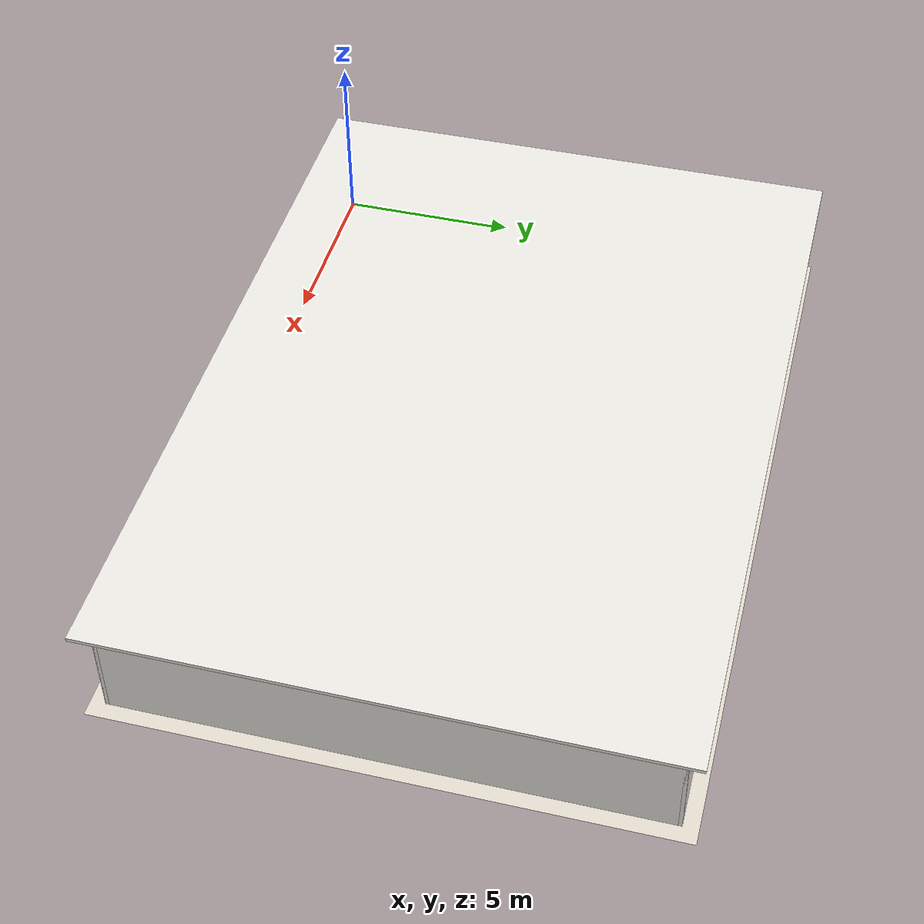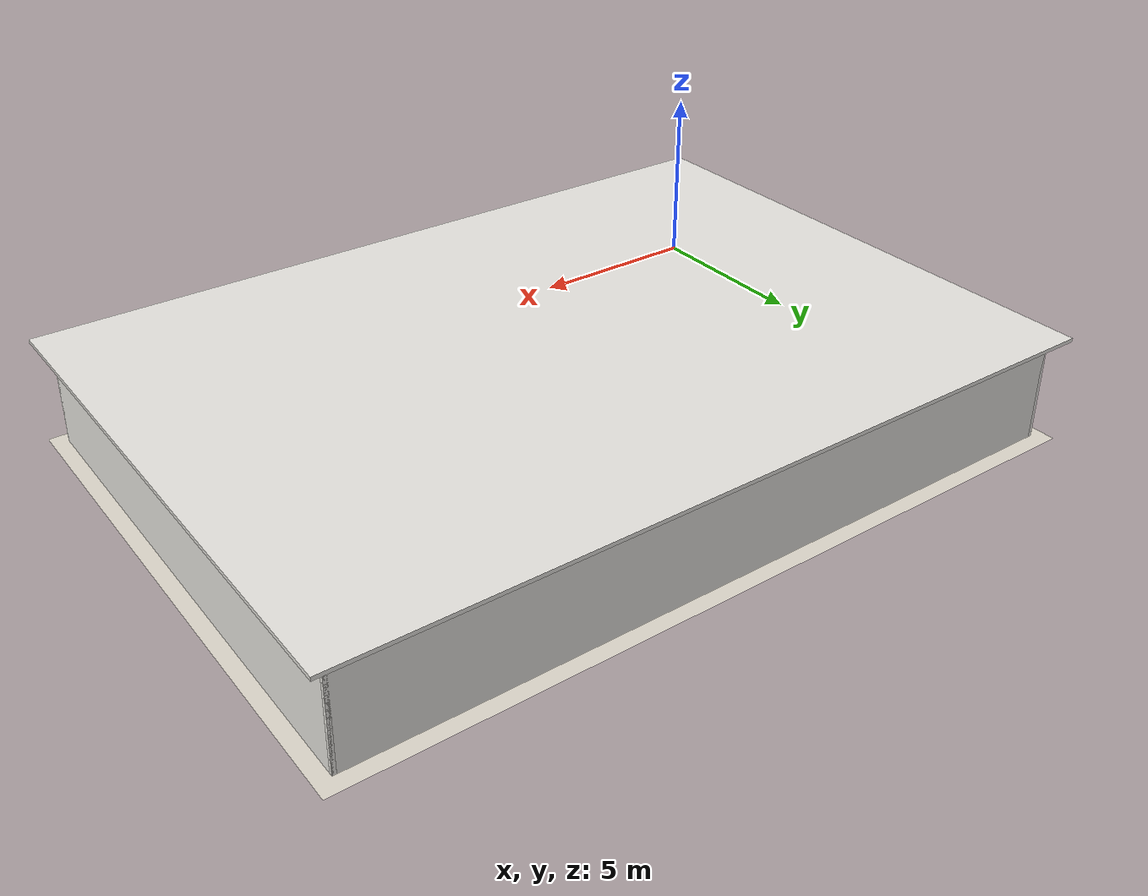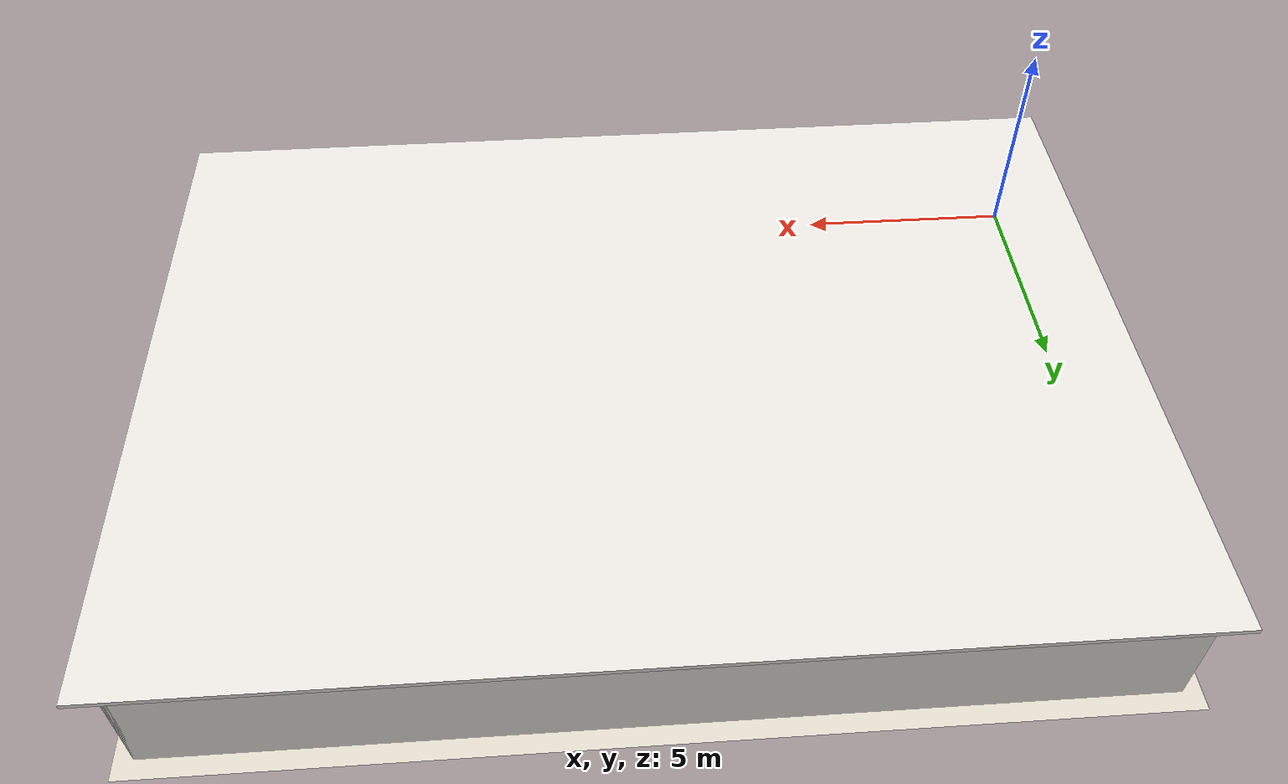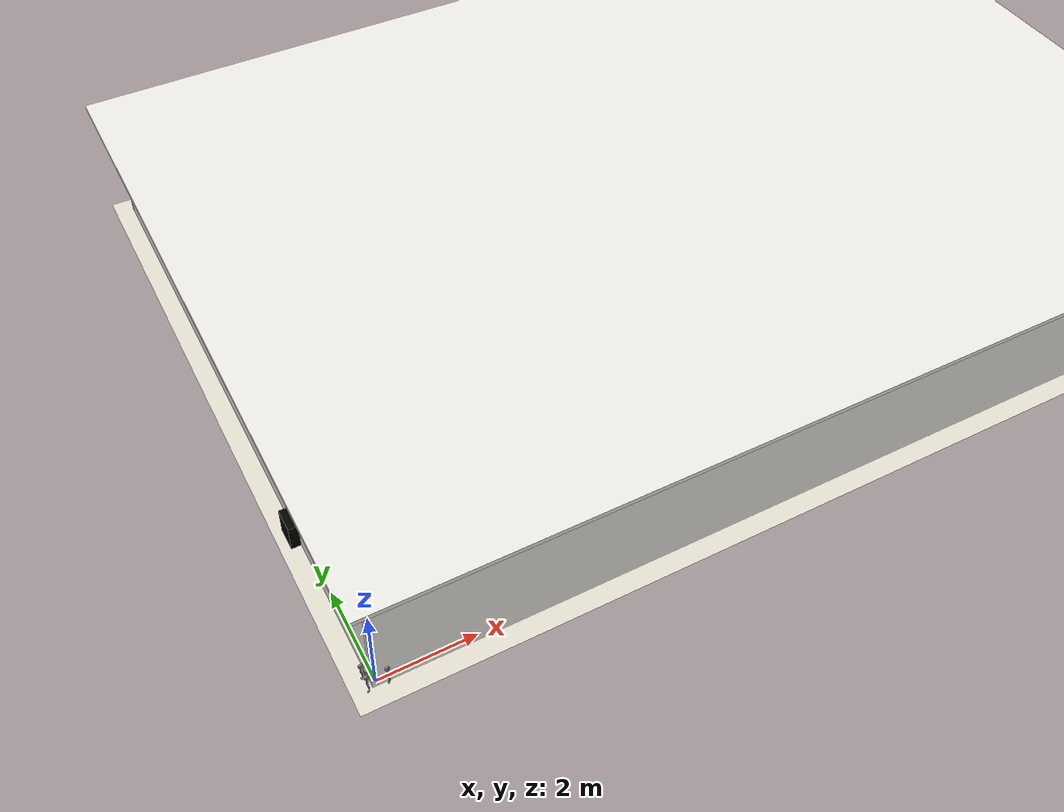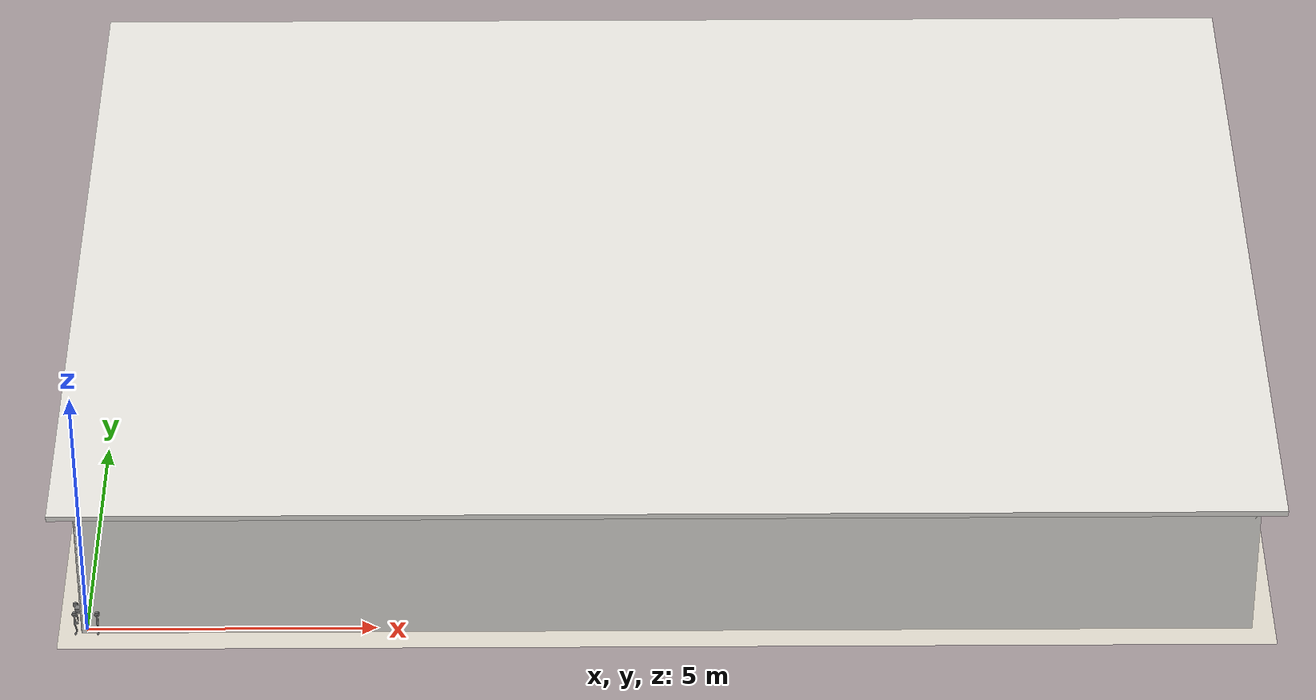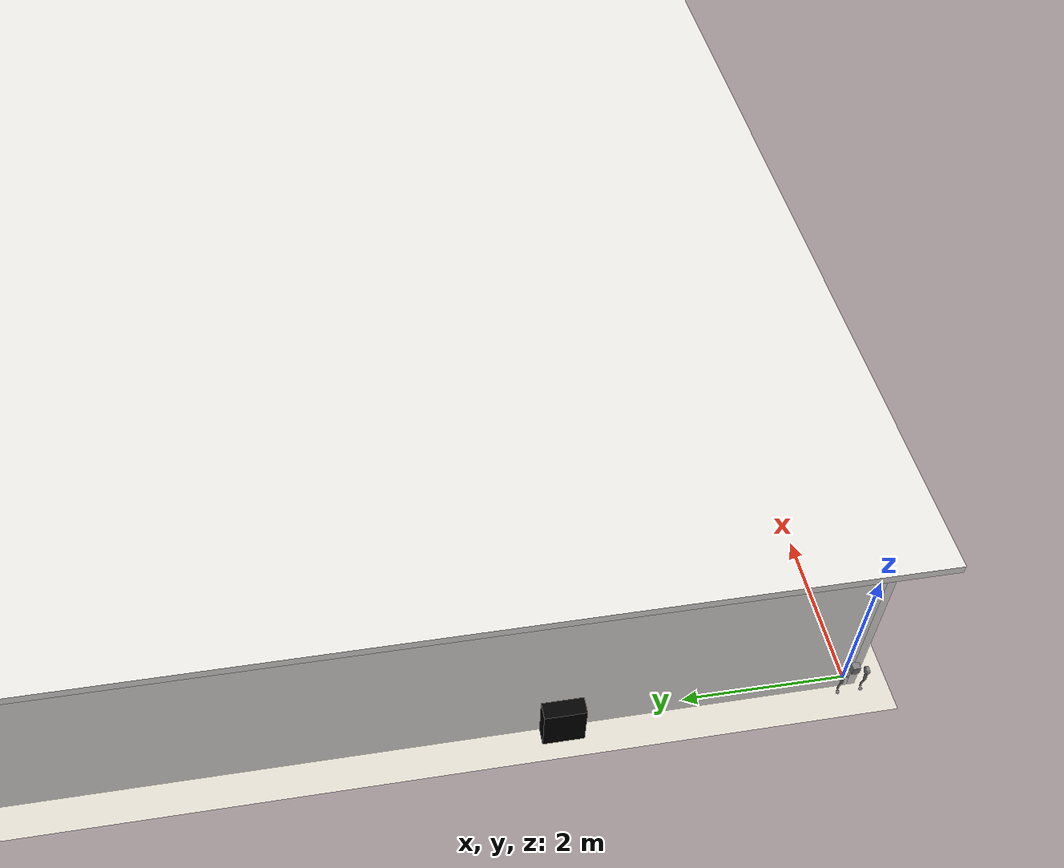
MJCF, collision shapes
<mujoco model="go2 house">
  <compiler angle="radian" meshdir="/home/yusen/Desktop/vector_os_nano/vector_os_nano/hardware/sim/assets" texturedir="/home/yusen/Desktop/vector_os_nano/vector_os_nano/hardware/sim/assets" autolimits="true"/>
  <include file="/home/yusen/Desktop/vector_os_nano/vector_os_nano/hardware/sim/go2.xml"/>

  <option cone="elliptic" impratio="100"/>

  <statistic center="10 7 0.5" extent="12"/>

  <visual>
    <headlight diffuse="0.5 0.5 0.5" ambient="0.4 0.4 0.4" specular="0 0 0"/>
    <rgba haze="0.15 0.25 0.35 1"/>
    <global azimuth="-120" elevation="-25" offwidth="1280" offheight="960"/>
    <map znear="0.05" zfar="50" shadowclip="0.5"/>
    <quality shadowsize="1024"/>
  </visual>

  <asset>
    <texture type="skybox" builtin="gradient" rgb1="0.88 0.90 0.95" rgb2="0.65 0.70 0.80"
             width="512" height="3072"/>

    <!-- Wall texture (subtle plaster) -->
    <texture type="2d" name="wall_tex" builtin="gradient"
             rgb1="0.94 0.93 0.91" rgb2="0.90 0.89 0.87" width="128" height="128"/>

    <!-- Floor textures -->
    <texture type="2d" name="wood_tex" builtin="checker"
             rgb1="0.78 0.68 0.48" rgb2="0.74 0.64 0.45" width="200" height="200"/>
    <texture type="2d" name="tile_tex" builtin="checker"
             rgb1="0.90 0.90 0.88" rgb2="0.80 0.80 0.78" width="150" height="150"/>
    <texture type="2d" name="carpet_tex" builtin="flat"
             rgb1="0.50 0.52 0.56" rgb2="0.45 0.47 0.51" width="100" height="100"/>
    <texture type="2d" name="marble_tex" builtin="checker"
             rgb1="0.92 0.90 0.85" rgb2="0.85 0.82 0.77" width="120" height="120"/>
    <texture type="2d" name="bath_tex" builtin="checker"
             rgb1="0.85 0.90 0.92" rgb2="0.75 0.80 0.82" width="80" height="80"/>

    <material name="wood_mat" texture="wood_tex" texuniform="true" texrepeat="10 10" reflectance="0.12"/>
    <material name="tile_mat" texture="tile_tex" texuniform="true" texrepeat="8 8" reflectance="0.25"/>
    <material name="carpet_mat" texture="carpet_tex" texuniform="true" texrepeat="3 3" reflectance="0.02"/>
    <material name="marble_mat" texture="marble_tex" texuniform="true" texrepeat="10 12" reflectance="0.2"/>
    <material name="bath_tile" texture="bath_tex" texuniform="true" texrepeat="6 6" reflectance="0.3"/>

    <material name="wall_mat" texture="wall_tex" texuniform="true" texrepeat="4 4" reflectance="0.04"/>
    <material name="accent_wall" rgba="0.82 0.85 0.90 1" reflectance="0.04"/>

    <!-- Furniture materials (used for collision boxes, some overrides) -->
    <material name="dark_wood" rgba="0.35 0.22 0.12 1" reflectance="0.12"/>
    <material name="rug_red" rgba="0.60 0.15 0.12 1" reflectance="0.02"/>
    <material name="rug_blue" rgba="0.15 0.25 0.45 1" reflectance="0.02"/>
    <material name="rug_beige" rgba="0.82 0.75 0.62 1" reflectance="0.02"/>
    <material name="painting_mat" rgba="0.85 0.65 0.40 1" reflectance="0.05"/>

    <!-- Furniture PNG textures (furniture_sim, Apache 2.0) -->
    <texture type="2d" name="tex_oak" file="furniture/wood2.png"/>
    <texture type="2d" name="tex_walnut" file="furniture/wood1.png"/>
    <texture type="2d" name="tex_cherry" file="furniture/wood4.png"/>
    <texture type="2d" name="tex_pine" file="furniture/wood0.png"/>
    <texture type="2d" name="tex_steel" file="furniture/metal0.png"/>
    <texture type="2d" name="tex_chrome" file="furniture/metal1.png"/>
    <texture type="2d" name="tex_marble" file="furniture/stone0.png"/>
    <texture type="2d" name="tex_ceramic" file="furniture/stone1.png"/>

    <!-- Textured furniture materials -->
    <material name="mat_oak" texture="tex_oak" texuniform="true" texrepeat="3 3" reflectance="0.12"/>
    <material name="mat_walnut" texture="tex_walnut" texuniform="true" texrepeat="3 3" reflectance="0.12"/>
    <material name="mat_cherry" texture="tex_cherry" texuniform="true" texrepeat="3 3" reflectance="0.10"/>
    <material name="mat_pine" texture="tex_pine" texuniform="true" texrepeat="4 4" reflectance="0.08"/>
    <material name="mat_steel" texture="tex_steel" texuniform="true" texrepeat="2 2" reflectance="0.40"/>
    <material name="mat_chrome" texture="tex_chrome" texuniform="true" texrepeat="2 2" reflectance="0.50"/>
    <material name="mat_marble" texture="tex_marble" texuniform="true" texrepeat="4 4" reflectance="0.25"/>
    <material name="mat_ceramic" texture="tex_ceramic" texuniform="true" texrepeat="3 3" reflectance="0.20"/>

    <!-- ==================== FURNITURE MESHES (Kenney CC0) ==================== -->
    <!-- Y-up OBJ → Z-up MuJoCo via euler="1.5708 0 0" on geom -->

    <!-- Sofa -->
    <mesh name="m_loungeSofa_carpet" file="furniture/loungeSofa_carpet.obj" scale="2.2 2.2 2.2" inertia="shell"/>
    <mesh name="m_loungeSofa_wood" file="furniture/loungeSofa_wood.obj" scale="2.2 2.2 2.2" inertia="shell"/>

    <!-- Coffee Table -->
    <mesh name="m_coffee_table" file="furniture/tableCoffee.obj" scale="1.8 1.8 1.8" inertia="shell"/>

    <!-- TV Console -->
    <mesh name="m_tv_console" file="furniture/cabinetTelevision.obj" scale="2.0 2.0 2.0" inertia="shell"/>

    <!-- TV -->
    <mesh name="m_televisionModern_metalDark" file="furniture/televisionModern_metalDark.obj" scale="1.7 1.7 1.7" inertia="shell"/>
    <mesh name="m_televisionModern_metal" inertia="shell" file="furniture/televisionModern_metal.obj" scale="1.7 1.7 1.7"/>

    <!-- Floor Lamp -->
    <mesh name="m_lampRoundFloor_metal" file="furniture/lampRoundFloor_metal.obj" scale="1.7 1.7 1.7" inertia="shell"/>
    <mesh name="m_lampRoundFloor_lamp" file="furniture/lampRoundFloor_lamp.obj" scale="1.7 1.7 1.7" inertia="shell"/>

    <!-- Rug -->
    <mesh name="m_rugRectangle_carpet" file="furniture/rugRectangle_carpet.obj" scale="2.0 2.0 2.0" inertia="shell"/>
    <mesh name="m_rugRectangle_carpetDarker" file="furniture/rugRectangle_carpetDarker.obj" scale="2.0 2.0 2.0" inertia="shell"/>

    <!-- Dining Table -->
    <mesh name="m_dining_table" file="furniture/table.obj" scale="2.0 2.0 2.0" inertia="shell"/>

    <!-- Chair -->
    <mesh name="m_chair" file="furniture/chair.obj" scale="2.1 2.1 2.1" inertia="shell"/>

    <!-- Potted Plant -->
    <!-- pottedPlant meshes removed — collision cylinders trap Go2 -->

    <!-- Sideboard -->
    <mesh name="m_sideTableDrawers_wood" file="furniture/sideTableDrawers_wood.obj" scale="2.0 2.0 2.0" inertia="shell"/>
    <mesh name="m_sideTableDrawers_defaultMat" inertia="shell" file="furniture/sideTableDrawers_defaultMat.obj" scale="2.0 2.0 2.0"/>
    <mesh name="m_sideTableDrawers_metal" inertia="shell" file="furniture/sideTableDrawers_metal.obj" scale="2.0 2.0 2.0"/>

    <!-- Kitchen Cabinet Drawer -->
    <mesh name="m_kitchenCabinetDrawer_metal" file="furniture/kitchenCabinetDrawer_metal.obj" scale="2.0 2.0 2.0" inertia="shell"/>
    <mesh name="m_kitchenCabinetDrawer_wood" file="furniture/kitchenCabinetDrawer_wood.obj" scale="2.0 2.0 2.0" inertia="shell"/>
    <mesh name="m_kitchenCabinetDrawer_woodDark" inertia="shell" file="furniture/kitchenCabinetDrawer_woodDark.obj" scale="2.0 2.0 2.0"/>

    <!-- Kitchen Stove -->
    <mesh name="m_kitchenStove_metal" file="furniture/kitchenStove_metal.obj" scale="2.0 2.0 2.0" inertia="shell"/>
    <mesh name="m_kitchenStove_wood" file="furniture/kitchenStove_wood.obj" scale="2.0 2.0 2.0" inertia="shell"/>
    <mesh name="m_kitchenStove_metalDark" file="furniture/kitchenStove_metalDark.obj" scale="2.0 2.0 2.0" inertia="shell"/>
    <mesh name="m_kitchenStove_carpetWhite" inertia="shell" file="furniture/kitchenStove_carpetWhite.obj" scale="2.0 2.0 2.0"/>
    <mesh name="m_kitchenStove_glass" inertia="shell" file="furniture/kitchenStove_glass.obj" scale="2.0 2.0 2.0"/>

    <!-- Fridge -->
    <mesh name="m_kitchenFridgeLarge_metalLight" file="furniture/kitchenFridgeLarge_metalLight.obj" scale="1.9 1.9 1.9" inertia="shell"/>
    <mesh name="m_kitchenFridgeLarge_metalMedium" file="furniture/kitchenFridgeLarge_metalMedium.obj" scale="1.9 1.9 1.9" inertia="shell"/>

    <!-- Bar Stool -->
    <mesh name="m_stoolBar_wood" file="furniture/stoolBar_wood.obj" scale="1.8 1.8 1.8" inertia="shell"/>
    <mesh name="m_stoolBar_carpet" file="furniture/stoolBar_carpet.obj" scale="1.8 1.8 1.8" inertia="shell"/>

    <!-- Desk -->
    <mesh name="m_desk_wood" file="furniture/desk_wood.obj" scale="2.0 2.0 2.0" inertia="shell"/>
    <mesh name="m_desk_metal" inertia="shell" file="furniture/desk_metal.obj" scale="2.0 2.0 2.0"/>

    <!-- Computer Screen -->
    <mesh name="m_computerScreen_metalDark" file="furniture/computerScreen_metalDark.obj" scale="1.6 1.6 1.6" inertia="shell"/>
    <mesh name="m_computerScreen_metal" file="furniture/computerScreen_metal.obj" scale="1.6 1.6 1.6" inertia="shell"/>

    <!-- Desk Chair -->
    <mesh name="m_chairDesk_metalMedium" file="furniture/chairDesk_metalMedium.obj" scale="1.7 1.7 1.7" inertia="shell"/>
    <mesh name="m_chairDesk_carpet" file="furniture/chairDesk_carpet.obj" scale="1.7 1.7 1.7" inertia="shell"/>

    <!-- Bookcase -->
    <mesh name="m_bookshelf" file="furniture/bookcaseOpen.obj" scale="2.0 2.0 2.0" inertia="shell"/>

    <!-- Double Bed -->
    <mesh name="m_bedDouble_carpet" file="furniture/bedDouble_carpet.obj" scale="2.0 2.0 2.0" inertia="shell"/>
    <mesh name="m_bedDouble_carpetWhite" file="furniture/bedDouble_carpetWhite.obj" scale="2.0 2.0 2.0" inertia="shell"/>
    <mesh name="m_bedDouble_metal" file="furniture/bedDouble_metal.obj" scale="2.0 2.0 2.0" inertia="shell"/>
    <mesh name="m_bedDouble_wood" file="furniture/bedDouble_wood.obj" scale="2.0 2.0 2.0" inertia="shell"/>

    <!-- Cabinet Bed Drawer (nightstand) -->
    <mesh name="m_cabinetBedDrawer_wood" file="furniture/cabinetBedDrawer_wood.obj" scale="1.9 1.9 1.9" inertia="shell"/>
    <mesh name="m_cabinetBedDrawer_defaultMat" inertia="shell" file="furniture/cabinetBedDrawer_defaultMat.obj" scale="1.9 1.9 1.9"/>
    <mesh name="m_cabinetBedDrawer_metal" file="furniture/cabinetBedDrawer_metal.obj" scale="1.9 1.9 1.9" inertia="shell"/>

    <!-- Single Bed -->
    <mesh name="m_bedSingle_carpet" file="furniture/bedSingle_carpet.obj" scale="1.7 1.7 1.7" inertia="shell"/>
    <mesh name="m_bedSingle_carpetWhite" file="furniture/bedSingle_carpetWhite.obj" scale="1.7 1.7 1.7" inertia="shell"/>
    <mesh name="m_bedSingle_metal" file="furniture/bedSingle_metal.obj" scale="1.7 1.7 1.7" inertia="shell"/>
    <mesh name="m_bedSingle_wood" file="furniture/bedSingle_wood.obj" scale="1.7 1.7 1.7" inertia="shell"/>

    <!-- Dresser (cabinetBedDrawerTable) -->
    <mesh name="m_dresser_wood" file="furniture/cabinetBedDrawerTable_wood.obj" scale="1.9 1.9 1.9" inertia="shell"/>
    <mesh name="m_dresser_defaultMat" file="furniture/cabinetBedDrawerTable_defaultMat.obj" scale="1.9 1.9 1.9" inertia="shell"/>
    <mesh name="m_dresser_metal" file="furniture/cabinetBedDrawerTable_metal.obj" scale="1.9 1.9 1.9" inertia="shell"/>

    <!-- Bathtub -->
    <mesh name="m_bathtub_carpetWhite" file="furniture/bathtub_carpetWhite.obj" scale="1.4 1.4 1.4" inertia="shell"/>
    <mesh name="m_bathtub_metalLight" file="furniture/bathtub_metalLight.obj" scale="1.4 1.4 1.4" inertia="shell"/>
    <mesh name="m_bathtub_metalDark" inertia="shell" file="furniture/bathtub_metalDark.obj" scale="1.4 1.4 1.4"/>

    <!-- Bathroom Sink (vanity) -->
    <mesh name="m_bathroomSink_defaultMat" file="furniture/bathroomSink_defaultMat.obj" scale="1.5 1.5 1.5" inertia="shell"/>
    <mesh name="m_bathroomSink_metalLight" file="furniture/bathroomSink_metalLight.obj" scale="1.5 1.5 1.5" inertia="shell"/>
    <mesh name="m_bathroomSink_carpetWhite" inertia="shell" file="furniture/bathroomSink_carpetWhite.obj" scale="1.5 1.5 1.5"/>

    <!-- Washer -->
    <mesh name="m_washer_metalLight" file="furniture/washer_metalLight.obj" scale="1.7 1.7 1.7" inertia="shell"/>
    <mesh name="m_washer_metalMedium" file="furniture/washer_metalMedium.obj" scale="1.7 1.7 1.7" inertia="shell"/>
    <mesh name="m_washer_metalDark" inertia="shell" file="furniture/washer_metalDark.obj" scale="1.7 1.7 1.7"/>
    <mesh name="m_washer_metal" file="furniture/washer_metal.obj" scale="1.7 1.7 1.7" inertia="shell"/>
    <mesh name="m_washer_glass" inertia="shell" file="furniture/washer_glass.obj" scale="1.7 1.7 1.7"/>
    <mesh name="m_washer_defaultMat" inertia="shell" file="furniture/washer_defaultMat.obj" scale="1.7 1.7 1.7"/>

    <!-- Dryer -->
    <mesh name="m_dryer_metalLight" file="furniture/dryer_metalLight.obj" scale="1.7 1.7 1.7" inertia="shell"/>
    <mesh name="m_dryer_metalMedium" file="furniture/dryer_metalMedium.obj" scale="1.7 1.7 1.7" inertia="shell"/>
    <mesh name="m_dryer_metalDark" inertia="shell" file="furniture/dryer_metalDark.obj" scale="1.7 1.7 1.7"/>

    <!-- Side Table (hallway console) -->
    <mesh name="m_sideTable_wood" file="furniture/sideTable_wood.obj" scale="1.8 1.8 1.8" inertia="shell"/>
    <mesh name="m_sideTable_defaultMat" inertia="shell" file="furniture/sideTable_defaultMat.obj" scale="1.8 1.8 1.8"/>
  </asset>

  <worldbody>
    <!-- ==================== LIGHTING ==================== -->
    <light name="light_living" pos="3 2.5 2.7" dir="0 0 -1" diffuse="0.55 0.50 0.42" cutoff="65" castshadow="false"/>
    <light name="light_dining" pos="3 7.5 2.7" dir="0 0 -1" diffuse="0.55 0.50 0.42" cutoff="65" castshadow="false"/>
    <light name="light_kitchen" pos="17 2.5 2.7" dir="0 0 -1" diffuse="0.60 0.58 0.52" cutoff="65" castshadow="false"/>
    <light name="light_study" pos="17 7.5 2.7" dir="0 0 -1" diffuse="0.55 0.52 0.45" cutoff="65" castshadow="false"/>
    <light name="light_hall_a" pos="10 3 2.7" dir="0 0 -1" diffuse="0.50 0.48 0.42" cutoff="55" castshadow="false"/>
    <light name="light_hall_b" pos="10 7 2.7" dir="0 0 -1" diffuse="0.50 0.48 0.42" cutoff="55" castshadow="false"/>
    <light name="light_master" pos="3.5 12 2.7" dir="0 0 -1" diffuse="0.50 0.45 0.38" cutoff="60" castshadow="false"/>
    <light name="light_guest" pos="16 12 2.7" dir="0 0 -1" diffuse="0.50 0.45 0.38" cutoff="60" castshadow="false"/>
    <light name="light_bath" pos="8.5 12 2.7" dir="0 0 -1" diffuse="0.55 0.55 0.55" cutoff="55" castshadow="false"/>
    <light name="sun" pos="10 7 4" dir="0 0 -1" directional="true" diffuse="0.35 0.35 0.35"/><!-- sun only shadow caster -->
    <light name="fill_hall" pos="10 5 0.5" dir="0 0 1" diffuse="0.15 0.14 0.12" castshadow="false"/>
    <light name="fill_living" pos="3 2.5 0.5" dir="0 0 1" diffuse="0.12 0.11 0.10" castshadow="false"/>
    <light name="fill_dining" pos="3 7.5 0.5" dir="0 0 1" diffuse="0.12 0.11 0.10" castshadow="false"/>
    <light name="fill_kitchen" pos="17 2.5 0.5" dir="0 0 1" diffuse="0.14 0.14 0.12" castshadow="false"/>

    <!-- ==================== FLOORS ==================== -->
    <geom name="floor" type="plane" pos="10 7 0" size="10.5 7.5 0.05" material="marble_mat"/>
    <geom name="floor_raycast" type="box" pos="10 7 -0.02" size="10.5 7.5 0.01"
          contype="0" conaffinity="0" group="3" rgba="0 0 0 0"/>
    <geom name="ceiling" type="box" pos="10 7 2.85" size="10.5 7.5 0.05" material="wall_mat"
          contype="0" conaffinity="0" group="3"/>
    <geom name="f_living" type="box" pos="3 2.5 0.001" size="3 2.5 0.001" material="wood_mat" contype="0" conaffinity="0"/>
    <geom name="f_dining" type="box" pos="3 7.5 0.001" size="3 2.5 0.001" material="wood_mat" contype="0" conaffinity="0"/>
    <geom name="f_kitchen" type="box" pos="17 2.5 0.001" size="3 2.5 0.001" material="tile_mat" contype="0" conaffinity="0"/>
    <geom name="f_study" type="box" pos="17 7.5 0.001" size="3 2.5 0.001" material="wood_mat" contype="0" conaffinity="0"/>
    <geom name="f_master" type="box" pos="3.5 12 0.001" size="3.5 2 0.001" material="carpet_mat" contype="0" conaffinity="0"/>
    <geom name="f_guest" type="box" pos="16 12 0.001" size="4 2 0.001" material="carpet_mat" contype="0" conaffinity="0"/>
    <geom name="f_bath" type="box" pos="8.5 12 0.001" size="1.5 2 0.001" material="bath_tile" contype="0" conaffinity="0"/>

    <!-- ==================== EXTERIOR WALLS ==================== -->
    <geom name="ew_south" type="box" pos="10 -0.05 1.4" size="10.1 0.05 1.4" material="wall_mat"/>
    <geom name="ew_north" type="box" pos="10 14.05 1.4" size="10.1 0.05 1.4" material="wall_mat"/>
    <geom name="ew_west" type="box" pos="-0.05 7 1.4" size="0.05 7.1 1.4" material="wall_mat"/>
    <geom name="ew_east" type="box" pos="20.05 7 1.4" size="0.05 7.1 1.4" material="wall_mat"/>

    <!-- ==================== INTERIOR WALLS ==================== -->
    <geom name="iw_l1" type="box" pos="6 1.2 1.4" size="0.05 1.2 1.4" material="accent_wall"/>
    <geom name="iw_l2" type="box" pos="6 4.3 1.4" size="0.05 0.7 1.4" material="accent_wall"/>
    <geom name="iw_l3" type="box" pos="6 6.2 1.4" size="0.05 1.2 1.4" material="accent_wall"/>
    <geom name="iw_l4" type="box" pos="6 9.3 1.4" size="0.05 0.7 1.4" material="accent_wall"/>
    <geom name="iw_r1" type="box" pos="14 1.2 1.4" size="0.05 1.2 1.4" material="accent_wall"/>
    <geom name="iw_r2" type="box" pos="14 4.3 1.4" size="0.05 0.7 1.4" material="accent_wall"/>
    <geom name="iw_r3" type="box" pos="14 6.2 1.4" size="0.05 1.2 1.4" material="accent_wall"/>
    <geom name="iw_r4" type="box" pos="14 9.3 1.4" size="0.05 0.7 1.4" material="accent_wall"/>
    <geom name="iw_ld1" type="box" pos="1.2 5 1.4" size="1.2 0.05 1.4" material="accent_wall"/>
    <geom name="iw_ld2" type="box" pos="4.8 5 1.4" size="1.2 0.05 1.4" material="accent_wall"/>
    <geom name="iw_ks1" type="box" pos="15.2 5 1.4" size="1.2 0.05 1.4" material="accent_wall"/>
    <geom name="iw_ks2" type="box" pos="18.8 5 1.4" size="1.2 0.05 1.4" material="accent_wall"/>
    <geom name="iw_b1" type="box" pos="1.2 10 1.4" size="1.2 0.05 1.4" material="wall_mat"/>
    <geom name="iw_b2" type="box" pos="4.8 10 1.4" size="1.2 0.05 1.4" material="wall_mat"/>
    <geom name="iw_b3" type="box" pos="6.95 10 1.4" size="0.95 0.05 1.4" material="wall_mat"/>
    <geom name="iw_b4" type="box" pos="10.55 10 1.4" size="1.45 0.05 1.4" material="wall_mat"/><!-- sealed laundry door -->
    <geom name="iw_b5" type="box" pos="13.0 10 1.4" size="1.0 0.05 1.4" material="wall_mat"/>
    <geom name="iw_b6" type="box" pos="14.7 10 1.4" size="0.7 0.05 1.4" material="wall_mat"/>
    <geom name="iw_b7" type="box" pos="18.3 10 1.4" size="1.7 0.05 1.4" material="wall_mat"/>
    <geom name="iw_bath_w" type="box" pos="7 12 1.4" size="0.05 2.05 1.4" material="wall_mat"/>
    <!-- iw_bath_e REMOVED — bathroom + laundry merged into one room -->
    <geom name="iw_laund_e" type="box" pos="12 12 1.4" size="0.05 2.05 1.4" material="wall_mat"/>

    <!-- ==================== LIVING ROOM (x=0..6, y=0..5) ==================== -->

    <body name="sofa_main" pos="1.8 1.0 0">
      <geom type="mesh" mesh="m_loungeSofa_carpet" euler="1.5708 0 0" pos="1.08 0.45 0" rgba="0.94 0.37 0.34 1" contype="0" conaffinity="0"/>
      <geom type="mesh" mesh="m_loungeSofa_wood" euler="1.5708 0 0" pos="1.08 0.45 0" material="mat_walnut" contype="0" conaffinity="0"/>
      <geom type="box" pos="0 0 0.45" size="1.1 0.45 0.45" rgba="0 0 0 0" group="3"/>
    </body>

    <body name="coffee_tbl" pos="1.8 2.3 0">
      <geom type="mesh" mesh="m_coffee_table" euler="1.5708 0 0" pos="-0.24 0.18 0" rgba="0.90 0.60 0.39 1" contype="0" conaffinity="0"/>
      <geom type="box" pos="0 0 0.20" size="0.6 0.35 0.20" rgba="0 0 0 0" group="3"/>
    </body>

    <body name="tv_console" pos="0.5 3.5 0">
      <geom type="mesh" mesh="m_tv_console" euler="1.5708 0 0" pos="0.80 0.25 0" rgba="0.90 0.60 0.39 1" contype="0" conaffinity="0"/>
      <geom type="box" pos="0 0 0.30" size="0.8 0.25 0.30" rgba="0 0 0 0" group="3"/>
    </body>

    <body name="tv_screen" pos="0.5 3.5 0.62">
      <geom type="mesh" mesh="m_televisionModern_metalDark" euler="1.5708 0 0" rgba="0.31 0.39 0.39 1" contype="0" conaffinity="0"/>
      <geom type="mesh" mesh="m_televisionModern_metal" euler="1.5708 0 0" rgba="0.74 0.82 0.84 1" contype="0" conaffinity="0"/>
    </body>

    <body name="lamp_living" pos="0.4 4.2 0">
      <geom type="mesh" mesh="m_lampRoundFloor_metal" euler="1.5708 0 0" pos="0.10 0.10 0" material="mat_chrome" contype="0" conaffinity="0"/>
      <geom type="mesh" mesh="m_lampRoundFloor_lamp" euler="1.5708 0 0" pos="0.10 0.10 0" rgba="1.0 0.91 0.59 1" contype="0" conaffinity="0"/>
      <geom type="cylinder" pos="0 0 0.7" size="0.12 0.7" rgba="0 0 0 0" group="3"/>
    </body>

    <geom name="rug_living_carpet" type="mesh" mesh="m_rugRectangle_carpet" euler="1.5708 0 0" pos="2.0 2.0 0.005"
          rgba="0.94 0.37 0.34 1" contype="0" conaffinity="0"/>
    <geom name="rug_living_darker" type="mesh" mesh="m_rugRectangle_carpetDarker" euler="1.5708 0 0" pos="2.0 2.0 0.005"
          rgba="0.61 0.30 0.29 1" contype="0" conaffinity="0"/>

    <geom name="art_living" type="box" pos="0.02 2.5 1.5" size="0.02 0.4 0.3"
          material="painting_mat" contype="0" conaffinity="0"/>

    <!-- ==================== DINING ROOM (x=0..6, y=5..10) ==================== -->

    <body name="dining_table" pos="3 7.5 0">
      <geom type="mesh" mesh="m_dining_table" euler="1.5708 0 0" pos="0.84 0.45 0" rgba="0.90 0.60 0.39 1" contype="0" conaffinity="0"/>
      <geom type="box" pos="0 0 0.33" size="0.84 0.45 0.33" rgba="0 0 0 0" group="3"/>
    </body>

    <body name="dchair1" pos="2.0 7.5 0">
      <geom type="mesh" mesh="m_chair" euler="1.5708 0 0" pos="0.21 0.21 0" material="mat_oak" contype="0" conaffinity="0"/>
      <geom type="box" pos="0 0 0.45" size="0.21 0.21 0.45" rgba="0 0 0 0" group="3"/>
    </body>
    <body name="dchair2" pos="4.0 7.5 0">
      <geom type="mesh" mesh="m_chair" euler="1.5708 0 3.1416" pos="-0.21 -0.21 0" material="mat_oak" contype="0" conaffinity="0"/>
      <geom type="box" pos="0 0 0.45" size="0.21 0.21 0.45" rgba="0 0 0 0" group="3"/>
    </body>
    <body name="dchair3" pos="3.0 6.7 0">
      <geom type="mesh" mesh="m_chair" euler="1.5708 0 1.5708" pos="0.21 -0.21 0" material="mat_oak" contype="0" conaffinity="0"/>
      <geom type="box" pos="0 0 0.45" size="0.21 0.21 0.45" rgba="0 0 0 0" group="3"/>
    </body>
    <body name="dchair4" pos="3.0 8.3 0">
      <geom type="mesh" mesh="m_chair" euler="1.5708 0 -1.5708" pos="-0.21 0.21 0" material="mat_oak" contype="0" conaffinity="0"/>
      <geom type="box" pos="0 0 0.45" size="0.21 0.21 0.45" rgba="0 0 0 0" group="3"/>
    </body>

    <body name="sideboard" pos="0.5 8.5 0">
      <geom type="mesh" mesh="m_sideTableDrawers_wood" euler="1.5708 0 0" pos="0.51 0.20 0" material="mat_cherry" contype="0" conaffinity="0"/>
      <geom type="mesh" mesh="m_sideTableDrawers_defaultMat" euler="1.5708 0 0" pos="0.51 0.20 0" rgba="1.0 1.0 1.0 1" contype="0" conaffinity="0"/>
      <geom type="mesh" mesh="m_sideTableDrawers_metal" euler="1.5708 0 0" pos="0.51 0.20 0" rgba="0.74 0.82 0.84 1" contype="0" conaffinity="0"/>
      <geom type="box" pos="0 0 0.38" size="0.53 0.22 0.38" rgba="0 0 0 0" group="3"/>
    </body>

    <!-- plant_dining REMOVED — collision cylinder traps Go2 -->

    <!-- ==================== KITCHEN (x=14..20, y=0..5) ==================== -->

    <body name="counter_east" pos="19.2 1.0 0">
      <geom type="mesh" mesh="m_kitchenCabinetDrawer_metal" euler="1.5708 0 0" pos="0.43 0.45 0" material="mat_chrome" contype="0" conaffinity="0"/>
      <geom type="mesh" mesh="m_kitchenCabinetDrawer_wood" euler="1.5708 0 0" pos="0.43 0.45 0" material="mat_cherry" contype="0" conaffinity="0"/>
      <geom type="mesh" mesh="m_kitchenCabinetDrawer_woodDark" euler="1.5708 0 0" pos="0.43 0.45 0" material="mat_walnut" contype="0" conaffinity="0"/>
      <geom type="box" pos="0 0 0.45" size="0.43 0.45 0.45" rgba="0 0 0 0" group="3"/>
    </body>
    <body name="counter_east2" pos="19.2 2.0 0">
      <geom type="mesh" mesh="m_kitchenCabinetDrawer_metal" euler="1.5708 0 0" pos="0.43 0.45 0" material="mat_chrome" contype="0" conaffinity="0"/>
      <geom type="mesh" mesh="m_kitchenCabinetDrawer_wood" euler="1.5708 0 0" pos="0.43 0.45 0" material="mat_cherry" contype="0" conaffinity="0"/>
      <geom type="mesh" mesh="m_kitchenCabinetDrawer_woodDark" euler="1.5708 0 0" pos="0.43 0.45 0" material="mat_walnut" contype="0" conaffinity="0"/>
      <geom type="box" pos="0 0 0.45" size="0.43 0.45 0.45" rgba="0 0 0 0" group="3"/>
    </body>
    <body name="counter_east3" pos="19.2 3.0 0">
      <geom type="mesh" mesh="m_kitchenCabinetDrawer_metal" euler="1.5708 0 0" pos="0.43 0.45 0" material="mat_chrome" contype="0" conaffinity="0"/>
      <geom type="mesh" mesh="m_kitchenCabinetDrawer_wood" euler="1.5708 0 0" pos="0.43 0.45 0" material="mat_cherry" contype="0" conaffinity="0"/>
      <geom type="mesh" mesh="m_kitchenCabinetDrawer_woodDark" euler="1.5708 0 0" pos="0.43 0.45 0" material="mat_walnut" contype="0" conaffinity="0"/>
      <geom type="box" pos="0 0 0.45" size="0.43 0.45 0.45" rgba="0 0 0 0" group="3"/>
    </body>

    <body name="counter_south" pos="15.5 0.5 0">
      <geom type="mesh" mesh="m_kitchenStove_metal" euler="1.5708 0 0" pos="0.43 0.45 0" material="mat_steel" contype="0" conaffinity="0"/>
      <geom type="mesh" mesh="m_kitchenStove_wood" euler="1.5708 0 0" pos="0.43 0.45 0" material="mat_cherry" contype="0" conaffinity="0"/>
      <geom type="mesh" mesh="m_kitchenStove_metalDark" euler="1.5708 0 0" pos="0.43 0.45 0" rgba="0.31 0.39 0.39 1" contype="0" conaffinity="0"/>
      <geom type="mesh" mesh="m_kitchenStove_carpetWhite" euler="1.5708 0 0" pos="0.43 0.45 0" rgba="0.97 1.0 1.0 1" contype="0" conaffinity="0"/>
      <geom type="mesh" mesh="m_kitchenStove_glass" euler="1.5708 0 0" pos="0.43 0.45 0" rgba="0.70 0.83 0.77 1" contype="0" conaffinity="0"/>
      <geom type="box" pos="0 0 0.45" size="0.43 0.45 0.45" rgba="0 0 0 0" group="3"/>
    </body>

    <body name="counter_south2" pos="16.5 0.5 0">
      <geom type="mesh" mesh="m_kitchenCabinetDrawer_metal" euler="1.5708 0 0" pos="0.43 0.45 0" material="mat_chrome" contype="0" conaffinity="0"/>
      <geom type="mesh" mesh="m_kitchenCabinetDrawer_wood" euler="1.5708 0 0" pos="0.43 0.45 0" material="mat_cherry" contype="0" conaffinity="0"/>
      <geom type="mesh" mesh="m_kitchenCabinetDrawer_woodDark" euler="1.5708 0 0" pos="0.43 0.45 0" material="mat_walnut" contype="0" conaffinity="0"/>
      <geom type="box" pos="0 0 0.45" size="0.43 0.45 0.45" rgba="0 0 0 0" group="3"/>
    </body>

    <body name="island" pos="17 2.8 0">
      <geom type="mesh" mesh="m_kitchenCabinetDrawer_metal" euler="1.5708 0 1.5708" pos="0.45 -0.43 0" material="mat_chrome" contype="0" conaffinity="0"/>
      <geom type="mesh" mesh="m_kitchenCabinetDrawer_wood" euler="1.5708 0 1.5708" pos="0.45 -0.43 0" material="mat_cherry" contype="0" conaffinity="0"/>
      <geom type="mesh" mesh="m_kitchenCabinetDrawer_woodDark" euler="1.5708 0 1.5708" pos="0.45 -0.43 0" material="mat_walnut" contype="0" conaffinity="0"/>
      <geom type="box" pos="0 0 0.45" size="0.43 0.45 0.45" rgba="0 0 0 0" group="3"/>
    </body>

    <body name="fridge" pos="19.2 4.3 0">
      <geom type="mesh" mesh="m_kitchenFridgeLarge_metalLight" euler="1.5708 0 0" pos="0.49 0.26 0" material="mat_steel" contype="0" conaffinity="0"/>
      <geom type="mesh" mesh="m_kitchenFridgeLarge_metalMedium" euler="1.5708 0 0" pos="0.49 0.26 0" material="mat_chrome" contype="0" conaffinity="0"/>
      <geom type="box" pos="0 0 0.88" size="0.5 0.38 0.88" rgba="0 0 0 0" group="3"/>
    </body>

    <body name="stool1" pos="16.0 2.8 0">
      <geom type="mesh" mesh="m_stoolBar_wood" euler="1.5708 0 0" pos="0.24 0.21 0" material="mat_oak" contype="0" conaffinity="0"/>
      <geom type="mesh" mesh="m_stoolBar_carpet" euler="1.5708 0 0" pos="0.24 0.21 0" rgba="0.94 0.37 0.34 1" contype="0" conaffinity="0"/>
      <geom type="cylinder" pos="0 0 0.38" size="0.17 0.38" rgba="0 0 0 0" group="3"/>
    </body>
    <body name="stool2" pos="18.0 2.8 0">
      <geom type="mesh" mesh="m_stoolBar_wood" euler="1.5708 0 0" pos="0.24 0.21 0" material="mat_oak" contype="0" conaffinity="0"/>
      <geom type="mesh" mesh="m_stoolBar_carpet" euler="1.5708 0 0" pos="0.24 0.21 0" rgba="0.94 0.37 0.34 1" contype="0" conaffinity="0"/>
      <geom type="cylinder" pos="0 0 0.38" size="0.17 0.38" rgba="0 0 0 0" group="3"/>
    </body>

    <!-- ==================== STUDY (x=14..20, y=5..10) ==================== -->

    <body name="desk" pos="19.0 7.5 0">
      <geom type="mesh" mesh="m_desk_wood" euler="1.5708 0 0" pos="0.71 0.37 0" material="mat_walnut" contype="0" conaffinity="0"/>
      <geom type="mesh" mesh="m_desk_metal" euler="1.5708 0 0" pos="0.71 0.37 0" material="mat_chrome" contype="0" conaffinity="0"/>
      <geom type="box" pos="0 0 0.38" size="0.73 0.39 0.38" rgba="0 0 0 0" group="3"/>
    </body>

    <body name="monitor" pos="19.0 7.5 0.77">
      <geom type="mesh" mesh="m_computerScreen_metalDark" euler="1.5708 0 0" pos="0.31 0.08 0" rgba="0.31 0.39 0.39 1" contype="0" conaffinity="0"/>
      <geom type="mesh" mesh="m_computerScreen_metal" euler="1.5708 0 0" pos="0.31 0.08 0" rgba="0.74 0.82 0.84 1" contype="0" conaffinity="0"/>
    </body>

    <body name="desk_chair" pos="18.0 7.5 0">
      <geom type="mesh" mesh="m_chairDesk_metalMedium" euler="1.5708 0 0" pos="0.28 0.27 0" material="mat_chrome" contype="0" conaffinity="0"/>
      <geom type="mesh" mesh="m_chairDesk_carpet" euler="1.5708 0 0" pos="0.28 0.27 0" rgba="0.94 0.37 0.34 1" contype="0" conaffinity="0"/>
      <geom type="box" pos="0 0 0.50" size="0.28 0.27 0.50" rgba="0 0 0 0" group="3"/>
    </body>

    <body name="bookshelf" pos="17 5.3 0">
      <geom type="mesh" mesh="m_bookshelf" euler="1.5708 0 0" pos="0.40 0.25 0" rgba="0.90 0.60 0.39 1" contype="0" conaffinity="0"/>
      <geom type="box" pos="0 0 0.88" size="0.40 0.25 0.88" rgba="0 0 0 0" group="3"/>
    </body>

    <geom name="rug_study_carpet" type="mesh" mesh="m_rugRectangle_carpet" euler="1.5708 0 0" pos="17.5 7.5 0.005"
          rgba="0.94 0.37 0.34 1" contype="0" conaffinity="0"/>
    <geom name="rug_study_darker" type="mesh" mesh="m_rugRectangle_carpetDarker" euler="1.5708 0 0" pos="17.5 7.5 0.005"
          rgba="0.61 0.30 0.29 1" contype="0" conaffinity="0"/>

    <!-- plant_study REMOVED — collision cylinder traps Go2 -->

    <!-- ==================== MASTER BEDROOM (x=0..7, y=10..14) ==================== -->

    <body name="master_bed" pos="1.5 12 0">
      <geom type="mesh" mesh="m_bedDouble_carpet" euler="1.5708 0 0" pos="0.96 1.12 0" rgba="0.94 0.37 0.34 1" contype="0" conaffinity="0"/>
      <geom type="mesh" mesh="m_bedDouble_carpetWhite" euler="1.5708 0 0" pos="0.96 1.12 0" rgba="0.97 1.0 1.0 1" contype="0" conaffinity="0"/>
      <geom type="mesh" mesh="m_bedDouble_metal" euler="1.5708 0 0" pos="0.96 1.12 0" material="mat_chrome" contype="0" conaffinity="0"/>
      <geom type="mesh" mesh="m_bedDouble_wood" euler="1.5708 0 0" pos="0.96 1.12 0" material="mat_walnut" contype="0" conaffinity="0"/>
      <geom type="box" pos="0 0 0.35" size="0.96 1.12 0.35" rgba="0 0 0 0" group="3"/>
    </body>

    <body name="nightstand_l" pos="1.5 10.6 0">
      <geom type="mesh" mesh="m_cabinetBedDrawer_wood" euler="1.5708 0 0" pos="0.23 0.18 0" material="mat_walnut" contype="0" conaffinity="0"/>
      <geom type="mesh" mesh="m_cabinetBedDrawer_defaultMat" euler="1.5708 0 0" pos="0.23 0.18 0" rgba="1.0 1.0 1.0 1" contype="0" conaffinity="0"/>
      <geom type="mesh" mesh="m_cabinetBedDrawer_metal" euler="1.5708 0 0" pos="0.23 0.18 0" material="mat_chrome" contype="0" conaffinity="0"/>
      <geom type="box" pos="0 0 0.25" size="0.25 0.20 0.25" rgba="0 0 0 0" group="3"/>
    </body>
    <body name="nightstand_r" pos="1.5 13.4 0">
      <geom type="mesh" mesh="m_cabinetBedDrawer_wood" euler="1.5708 0 0" pos="0.23 0.18 0" material="mat_walnut" contype="0" conaffinity="0"/>
      <geom type="mesh" mesh="m_cabinetBedDrawer_defaultMat" euler="1.5708 0 0" pos="0.23 0.18 0" rgba="1.0 1.0 1.0 1" contype="0" conaffinity="0"/>
      <geom type="mesh" mesh="m_cabinetBedDrawer_metal" euler="1.5708 0 0" pos="0.23 0.18 0" material="mat_chrome" contype="0" conaffinity="0"/>
      <geom type="box" pos="0 0 0.25" size="0.25 0.20 0.25" rgba="0 0 0 0" group="3"/>
    </body>

    <body name="wardrobe" pos="5.5 13.3 0">
      <geom type="mesh" mesh="m_bookshelf" euler="1.5708 0 0" pos="0.40 0.25 0" rgba="0.90 0.60 0.39 1" contype="0" conaffinity="0"/>
      <geom type="box" pos="0 0 0.88" size="0.40 0.30 0.88" rgba="0 0 0 0" group="3"/>
    </body>

    <geom name="rug_master_carpet" type="mesh" mesh="m_rugRectangle_carpet" euler="1.5708 0 0" pos="3 12 0.005"
          rgba="0.94 0.37 0.34 1" contype="0" conaffinity="0"/>
    <geom name="rug_master_darker" type="mesh" mesh="m_rugRectangle_carpetDarker" euler="1.5708 0 0" pos="3 12 0.005"
          rgba="0.61 0.30 0.29 1" contype="0" conaffinity="0"/>

    <!-- ==================== GUEST BEDROOM (x=12..20, y=10..14) ==================== -->

    <body name="guest_bed" pos="17.5 12 0">
      <geom type="mesh" mesh="m_bedSingle_carpet" euler="1.5708 0 0" pos="1.14 0.96 0" rgba="0.94 0.37 0.34 1" contype="0" conaffinity="0"/>
      <geom type="mesh" mesh="m_bedSingle_carpetWhite" euler="1.5708 0 0" pos="1.14 0.96 0" rgba="0.97 1.0 1.0 1" contype="0" conaffinity="0"/>
      <geom type="mesh" mesh="m_bedSingle_metal" euler="1.5708 0 0" pos="1.14 0.96 0" material="mat_chrome" contype="0" conaffinity="0"/>
      <geom type="mesh" mesh="m_bedSingle_wood" euler="1.5708 0 0" pos="1.14 0.96 0" material="mat_oak" contype="0" conaffinity="0"/>
      <geom type="box" pos="0 0 0.32" size="0.5 0.96 0.32" rgba="0 0 0 0" group="3"/>
    </body>

    <body name="guest_nightstand" pos="16.3 12.5 0">
      <geom type="mesh" mesh="m_cabinetBedDrawer_wood" euler="1.5708 0 0" pos="0.23 0.18 0" material="mat_walnut" contype="0" conaffinity="0"/>
      <geom type="mesh" mesh="m_cabinetBedDrawer_defaultMat" euler="1.5708 0 0" pos="0.23 0.18 0" rgba="1.0 1.0 1.0 1" contype="0" conaffinity="0"/>
      <geom type="mesh" mesh="m_cabinetBedDrawer_metal" euler="1.5708 0 0" pos="0.23 0.18 0" material="mat_chrome" contype="0" conaffinity="0"/>
      <geom type="box" pos="0 0 0.25" size="0.25 0.20 0.25" rgba="0 0 0 0" group="3"/>
    </body>

    <body name="dresser" pos="13 13.3 0">
      <geom type="mesh" mesh="m_dresser_wood" euler="1.5708 0 0" pos="0.23 0.18 0" rgba="0.90 0.60 0.39 1" contype="0" conaffinity="0"/>
      <geom type="mesh" mesh="m_dresser_defaultMat" euler="1.5708 0 0" pos="0.23 0.18 0" rgba="1.0 1.0 1.0 1" contype="0" conaffinity="0"/>
      <geom type="mesh" mesh="m_dresser_metal" euler="1.5708 0 0" pos="0.23 0.18 0" rgba="0.74 0.82 0.84 1" contype="0" conaffinity="0"/>
      <geom type="box" pos="0 0 0.25" size="0.25 0.20 0.25" rgba="0 0 0 0" group="3"/>
    </body>

    <!-- ==================== BATHROOM (x=7..10, y=10..14) ==================== -->

    <body name="bathtub" pos="8.5 13.2 0">
      <geom type="mesh" mesh="m_bathtub_carpetWhite" euler="1.5708 0 0" pos="0.83 0.39 0" material="mat_ceramic" contype="0" conaffinity="0"/>
      <geom type="mesh" mesh="m_bathtub_metalLight" euler="1.5708 0 0" pos="0.83 0.39 0" material="mat_ceramic" contype="0" conaffinity="0"/>
      <geom type="mesh" mesh="m_bathtub_metalDark" euler="1.5708 0 0" pos="0.83 0.39 0" rgba="0.31 0.39 0.39 1" contype="0" conaffinity="0"/>
      <geom type="box" pos="0 0 0.30" size="0.83 0.39 0.30" rgba="0 0 0 0" group="3"/>
    </body>

    <body name="vanity" pos="7.5 11 0">
      <geom type="mesh" mesh="m_bathroomSink_defaultMat" euler="1.5708 0 0" pos="0.26 0.22 0" material="mat_ceramic" contype="0" conaffinity="0"/>
      <geom type="mesh" mesh="m_bathroomSink_metalLight" euler="1.5708 0 0" pos="0.26 0.22 0" material="mat_chrome" contype="0" conaffinity="0"/>
      <geom type="mesh" mesh="m_bathroomSink_carpetWhite" euler="1.5708 0 0" pos="0.26 0.22 0" material="mat_ceramic" contype="0" conaffinity="0"/>
      <geom type="box" pos="0 0 0.42" size="0.26 0.22 0.42" rgba="0 0 0 0" group="3"/>
    </body>

    <!-- ==================== LAUNDRY (merged into bathroom, x=7..12, y=10..14) ==================== -->

    <body name="washer" pos="11 11 0">
      <geom type="mesh" mesh="m_washer_metalLight" euler="1.5708 0 0" pos="0.33 0.26 0" material="mat_steel" contype="0" conaffinity="0"/>
      <geom type="mesh" mesh="m_washer_metalMedium" euler="1.5708 0 0" pos="0.33 0.26 0" material="mat_chrome" contype="0" conaffinity="0"/>
      <geom type="mesh" mesh="m_washer_metalDark" euler="1.5708 0 0" pos="0.33 0.26 0" rgba="0.31 0.39 0.39 1" contype="0" conaffinity="0"/>
      <geom type="mesh" mesh="m_washer_metal" euler="1.5708 0 0" pos="0.33 0.26 0" material="mat_chrome" contype="0" conaffinity="0"/>
      <geom type="mesh" mesh="m_washer_glass" euler="1.5708 0 0" pos="0.33 0.26 0" rgba="0.70 0.83 0.77 1" contype="0" conaffinity="0"/>
      <geom type="mesh" mesh="m_washer_defaultMat" euler="1.5708 0 0" pos="0.33 0.26 0" rgba="1.0 1.0 1.0 1" contype="0" conaffinity="0"/>
      <geom type="box" pos="0 0 0.40" size="0.33 0.33 0.40" rgba="0 0 0 0" group="3"/>
    </body>
    <body name="dryer_unit" pos="11 12 0">
      <geom type="mesh" mesh="m_dryer_metalLight" euler="1.5708 0 0" pos="0.33 0.27 0" material="mat_steel" contype="0" conaffinity="0"/>
      <geom type="mesh" mesh="m_dryer_metalMedium" euler="1.5708 0 0" pos="0.33 0.27 0" material="mat_chrome" contype="0" conaffinity="0"/>
      <geom type="mesh" mesh="m_dryer_metalDark" euler="1.5708 0 0" pos="0.33 0.27 0" rgba="0.31 0.39 0.39 1" contype="0" conaffinity="0"/>
      <geom type="box" pos="0 0 0.40" size="0.33 0.33 0.40" rgba="0 0 0 0" group="3"/>
    </body>

    <!-- ==================== CENTRAL HALLWAY DECOR ==================== -->

    <body name="console_table" pos="6.5 5 0">
      <geom type="mesh" mesh="m_sideTable_wood" euler="1.5708 0 0" pos="0.46 0.18 0" material="mat_cherry" contype="0" conaffinity="0"/>
      <geom type="mesh" mesh="m_sideTable_defaultMat" euler="1.5708 0 0" pos="0.46 0.18 0" rgba="1.0 1.0 1.0 1" contype="0" conaffinity="0"/>
      <geom type="box" pos="0 0 0.35" size="0.48 0.20 0.35" rgba="0 0 0 0" group="3"/>
    </body>

    <!-- plant_entry REMOVED — collision cylinder in hallway traps Go2 -->

    <geom name="rug_hall_carpet" type="mesh" mesh="m_rugRectangle_carpet" euler="1.5708 0 1.5708" pos="10 5 0.005"
          rgba="0.94 0.37 0.34 1" contype="0" conaffinity="0"/>
    <geom name="rug_hall_darker" type="mesh" mesh="m_rugRectangle_carpetDarker" euler="1.5708 0 1.5708" pos="10 5 0.005"
          rgba="0.61 0.30 0.29 1" contype="0" conaffinity="0"/>

    <!-- plant_hall REMOVED — collision cylinder in hallway traps Go2 -->

    <geom name="art_hall1" type="box" pos="6.02 3 1.5" size="0.015 0.35 0.25"
          material="painting_mat" contype="0" conaffinity="0"/>
    <geom name="art_hall2" type="box" pos="13.98 6.5 1.5" size="0.015 0.4 0.3"
          material="painting_mat" contype="0" conaffinity="0"/>

    <!-- ==================== BASEBOARDS (visual only) ==================== -->
    <geom name="bb_south" type="box" pos="10 0.06 0.04" size="10.0 0.01 0.04"
          material="dark_wood" contype="0" conaffinity="0"/>
    <geom name="bb_north" type="box" pos="10 13.94 0.04" size="10.0 0.01 0.04"
          material="dark_wood" contype="0" conaffinity="0"/>
    <geom name="bb_west" type="box" pos="0.06 7 0.04" size="0.01 7.0 0.04"
          material="dark_wood" contype="0" conaffinity="0"/>
    <geom name="bb_east" type="box" pos="19.94 7 0.04" size="0.01 7.0 0.04"
          material="dark_wood" contype="0" conaffinity="0"/>

    <!-- ==================== DOOR FRAMES (visual only) ==================== -->
    <geom name="df_living_l" type="box" pos="6 2.38 1.1" size="0.06 0.03 1.1" material="dark_wood" contype="0" conaffinity="0"/>
    <geom name="df_living_r" type="box" pos="6 3.62 1.1" size="0.06 0.03 1.1" material="dark_wood" contype="0" conaffinity="0"/>
    <geom name="df_living_t" type="box" pos="6 3.0 2.23" size="0.06 0.62 0.03" material="dark_wood" contype="0" conaffinity="0"/>
    <geom name="df_dining_l" type="box" pos="6 7.38 1.1" size="0.06 0.03 1.1" material="dark_wood" contype="0" conaffinity="0"/>
    <geom name="df_dining_r" type="box" pos="6 8.62 1.1" size="0.06 0.03 1.1" material="dark_wood" contype="0" conaffinity="0"/>
    <geom name="df_dining_t" type="box" pos="6 8.0 2.23" size="0.06 0.62 0.03" material="dark_wood" contype="0" conaffinity="0"/>
    <geom name="df_kitchen_l" type="box" pos="14 2.38 1.1" size="0.06 0.03 1.1" material="dark_wood" contype="0" conaffinity="0"/>
    <geom name="df_kitchen_r" type="box" pos="14 3.62 1.1" size="0.06 0.03 1.1" material="dark_wood" contype="0" conaffinity="0"/>
    <geom name="df_kitchen_t" type="box" pos="14 3.0 2.23" size="0.06 0.62 0.03" material="dark_wood" contype="0" conaffinity="0"/>
    <geom name="df_study_l" type="box" pos="14 7.38 1.1" size="0.06 0.03 1.1" material="dark_wood" contype="0" conaffinity="0"/>
    <geom name="df_study_r" type="box" pos="14 8.62 1.1" size="0.06 0.03 1.1" material="dark_wood" contype="0" conaffinity="0"/>
    <geom name="df_study_t" type="box" pos="14 8.0 2.23" size="0.06 0.62 0.03" material="dark_wood" contype="0" conaffinity="0"/>
    <geom name="df_ld_l" type="box" pos="2.38 5 1.1" size="0.03 0.06 1.1" material="dark_wood" contype="0" conaffinity="0"/>
    <geom name="df_ld_r" type="box" pos="3.62 5 1.1" size="0.03 0.06 1.1" material="dark_wood" contype="0" conaffinity="0"/>
    <geom name="df_ld_t" type="box" pos="3.0 5 2.23" size="0.62 0.06 0.03" material="dark_wood" contype="0" conaffinity="0"/>
    <geom name="df_ks_l" type="box" pos="16.38 5 1.1" size="0.03 0.06 1.1" material="dark_wood" contype="0" conaffinity="0"/>
    <geom name="df_ks_r" type="box" pos="17.62 5 1.1" size="0.03 0.06 1.1" material="dark_wood" contype="0" conaffinity="0"/>
    <geom name="df_ks_t" type="box" pos="17.0 5 2.23" size="0.62 0.06 0.03" material="dark_wood" contype="0" conaffinity="0"/>
    <geom name="df_master_l" type="box" pos="2.38 10 1.1" size="0.03 0.06 1.1" material="dark_wood" contype="0" conaffinity="0"/>
    <geom name="df_master_r" type="box" pos="3.62 10 1.1" size="0.03 0.06 1.1" material="dark_wood" contype="0" conaffinity="0"/>
    <geom name="df_master_t" type="box" pos="3.0 10 2.23" size="0.62 0.06 0.03" material="dark_wood" contype="0" conaffinity="0"/>
    <geom name="df_bath_l" type="box" pos="7.88 10 1.1" size="0.03 0.06 1.1" material="dark_wood" contype="0" conaffinity="0"/>
    <geom name="df_bath_r" type="box" pos="9.12 10 1.1" size="0.03 0.06 1.1" material="dark_wood" contype="0" conaffinity="0"/>
    <geom name="df_bath_t" type="box" pos="8.5 10 2.23" size="0.62 0.06 0.03" material="dark_wood" contype="0" conaffinity="0"/>
    <geom name="df_guest_l" type="box" pos="15.38 10 1.1" size="0.03 0.06 1.1" material="dark_wood" contype="0" conaffinity="0"/>
    <geom name="df_guest_r" type="box" pos="16.62 10 1.1" size="0.03 0.06 1.1" material="dark_wood" contype="0" conaffinity="0"/>
    <geom name="df_guest_t" type="box" pos="16.0 10 2.23" size="0.62 0.06 0.03" material="dark_wood" contype="0" conaffinity="0"/>

  </worldbody>
</mujoco>

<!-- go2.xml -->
<mujoco model="go2">
  <compiler angle="radian" meshdir="assets" autolimits="true" />

  <option cone="elliptic" impratio="100" />

  <default>
    <default class="go2">
      <geom friction="0.4" margin="0.001" condim="1"/>
      <joint axis="0 1 0" damping="0.1" armature="0.01" frictionloss="0.2"/>
      <motor ctrlrange="-23.7 23.7"/>
      <default class="abduction">
        <joint axis="1 0 0" range="-1.0472 1.0472"/>
      </default>
      <default class="hip">
        <default class="front_hip">
          <joint range="-1.5708 3.4907"/>
        </default>
        <default class="back_hip">
          <joint range="-0.5236 4.5379"/>
        </default>
      </default>
      <default class="knee">
        <joint range="-2.7227 -0.83776"/>
        <motor ctrlrange="-45.43 45.43"/>
      </default>
      <default class="visual">
        <geom type="mesh" contype="0" conaffinity="0" group="2"/>
      </default>
      <default class="collision">
        <geom group="3"/>
        <default class="foot">
          <geom size="0.022" pos="-0.002 0 -0.213" priority="1" condim="6"
            friction="0.8 0.02 0.01"/>
        </default>
      </default>
    </default>
  </default>

  <asset>
    <material name="metal" rgba=".9 .95 .95 1" />
    <material name="black" rgba="0 0 0 1" />
    <material name="white" rgba="1 1 1 1" />
    <material name="gray" rgba="0.671705 0.692426 0.774270 1" />

    <mesh file="base_0.obj" />
    <mesh file="base_1.obj" />
    <mesh file="base_2.obj" />
    <mesh file="base_3.obj" />
    <mesh file="base_4.obj" />
    <mesh file="hip_0.obj" />
    <mesh file="hip_1.obj" />
    <mesh file="thigh_0.obj" />
    <mesh file="thigh_1.obj" />
    <mesh file="thigh_mirror_0.obj" />
    <mesh file="thigh_mirror_1.obj" />
    <mesh file="calf_0.obj" />
    <mesh file="calf_1.obj" />
    <mesh file="calf_mirror_0.obj" />
    <mesh file="calf_mirror_1.obj" />
    <mesh file="foot.obj" />
  </asset>

  <worldbody>
    <body name="base_link" pos="0 0 0.445" childclass="go2">
      <inertial pos="0.021112 0 -0.005366" quat="-0.000543471 0.713435 -0.00173769 0.700719"
        mass="6.921"
        diaginertia="0.107027 0.0980771 0.0244531" />
      <freejoint />
      <geom mesh="base_0" material="black" class="visual" />
      <geom mesh="base_1" material="black" class="visual" />
      <geom mesh="base_2" material="black" class="visual" />
      <geom mesh="base_3" material="white" class="visual" />
      <geom mesh="base_4" material="gray" class="visual" />
      <geom size="0.1881 0.04675 0.057" type="box" class="collision" />
      <geom size="0.05 0.045" pos="0.285 0 0.01" type="cylinder" class="collision" />
      <geom size="0.047" pos="0.293 0 -0.06" class="collision" />
      <site name="imu" pos="-0.02557 0 0.04232" />

      <!-- Livox MID-360 — shoulder area, 20 deg FORWARD tilt -->
      <!-- pos: x=0.15 (shoulder), z=0.14 (on bracket above trunk top) -->
      <!-- euler: +0.349 rad around Y = forward lean (top tilts toward +X) -->
      <body name="mid360_lidar" pos="0.15 0.0 0.14" euler="0 0.349 0">
        <geom type="cylinder" size="0.012 0.04" pos="0 0 -0.04" rgba="0.4 0.4 0.4 1"
              mass="0.05" contype="0" conaffinity="0" />
        <geom type="cylinder" size="0.05 0.03" rgba="0.15 0.15 0.15 1" mass="0.265"
              contype="0" conaffinity="0" />
        <site name="mid360_site" pos="0 0 0.03" />
      </body>

      <!-- RealSense D435 — in front of lidar, HORIZONTAL (wide along Y) -->
      <!-- pos: x=0.25 (forward of lidar), z=0.10 (slightly lower) -->
      <!-- euler: +0.087 rad around Y = 5 deg nose-down -->
      <!-- box: 25mm deep (X) x 90mm wide (Y) x 25mm tall (Z) -->
      <body name="d435_camera" pos="0.25 0.0 0.10" euler="0 0.087 0">
        <geom type="box" size="0.0125 0.045 0.0125" rgba="0.15 0.15 0.15 1" mass="0.072"
              contype="0" conaffinity="0" />
        <geom type="cylinder" size="0.008 0.005" pos="0.0 0.02 0.0" euler="1.5708 0 0"
              rgba="0.1 0.1 0.3 1" contype="0" conaffinity="0" />
        <geom type="cylinder" size="0.008 0.005" pos="0.0 -0.02 0.0" euler="1.5708 0 0"
              rgba="0.1 0.1 0.3 1" contype="0" conaffinity="0" />
        <camera name="d435_rgb" pos="0 0 0" xyaxes="0 -1 0 0 0 1" fovy="42" />
        <camera name="d435_depth" pos="0 0 0" xyaxes="0 -1 0 0 0 1" fovy="42" />
      </body>
      <body name="FL_hip" pos="0.1934 0.0465 0">
        <inertial pos="-0.0054 0.00194 -0.000105" quat="0.497014 0.499245 0.505462 0.498237"
          mass="0.678"
          diaginertia="0.00088403 0.000596003 0.000479967" />
        <joint name="FL_hip_joint" class="abduction" />
        <geom mesh="hip_0" material="metal" class="visual" />
        <geom mesh="hip_1" material="gray" class="visual" />
        <geom size="0.046 0.02" pos="0 0.08 0" quat="1 1 0 0" type="cylinder" class="collision" />
        <body name="FL_thigh" pos="0 0.0955 0">
          <inertial pos="-0.00374 -0.0223 -0.0327" quat="0.829533 0.0847635 -0.0200632 0.551623"
            mass="1.152"
            diaginertia="0.00594973 0.00584149 0.000878787" />
          <joint name="FL_thigh_joint" class="front_hip" />
          <geom mesh="thigh_0" material="metal" class="visual" />
          <geom mesh="thigh_1" material="gray" class="visual" />
          <geom size="0.1065 0.01225 0.017" pos="0 0 -0.1065" quat="0.707107 0 0.707107 0"
            type="box" class="collision" />
          <body name="FL_calf" pos="0 0 -0.213">
            <inertial pos="0.00629595 -0.000622121 -0.141417"
              quat="0.710672 0.00154099 -0.00450087 0.703508"
              mass="0.241352" diaginertia="0.0014901 0.00146356 5.31397e-05" />
            <joint name="FL_calf_joint" class="knee" />
            <geom mesh="calf_0" material="gray" class="visual" />
            <geom mesh="calf_1" material="black" class="visual" />
            <geom size="0.012 0.06" pos="0.008 0 -0.06" quat="0.994493 0 -0.104807 0"
              type="cylinder" class="collision" />
            <geom size="0.011 0.0325" pos="0.02 0 -0.148" quat="0.999688 0 0.0249974 0"
              type="cylinder" class="collision" />
            <geom pos="0 0 -0.213" mesh="foot" class="visual" material="black" />
            <geom name="FL" class="foot" />
            <body name="FL_foot" pos="0 0 -0.213" />
          </body>
        </body>
      </body>
      <body name="FR_hip" pos="0.1934 -0.0465 0">
        <inertial pos="-0.0054 -0.00194 -0.000105" quat="0.498237 0.505462 0.499245 0.497014"
          mass="0.678"
          diaginertia="0.00088403 0.000596003 0.000479967" />
        <joint name="FR_hip_joint" class="abduction" />
        <geom mesh="hip_0" material="metal" class="visual" quat="4.63268e-05 1 0 0" />
        <geom mesh="hip_1" material="gray" class="visual" quat="4.63268e-05 1 0 0" />
        <geom size="0.046 0.02" pos="0 -0.08 0" quat="0.707107 0.707107 0 0" type="cylinder"
          class="collision" />
        <body name="FR_thigh" pos="0 -0.0955 0">
          <inertial pos="-0.00374 0.0223 -0.0327" quat="0.551623 -0.0200632 0.0847635 0.829533"
            mass="1.152"
            diaginertia="0.00594973 0.00584149 0.000878787" />
          <joint name="FR_thigh_joint" class="front_hip" />
          <geom mesh="thigh_mirror_0" material="metal" class="visual" />
          <geom mesh="thigh_mirror_1" material="gray" class="visual" />
          <geom size="0.1065 0.01225 0.017" pos="0 0 -0.1065" quat="0.707107 0 0.707107 0"
            type="box" class="collision" />
          <body name="FR_calf" pos="0 0 -0.213">
            <inertial pos="0.00629595 0.000622121 -0.141417"
              quat="0.703508 -0.00450087 0.00154099 0.710672"
              mass="0.241352" diaginertia="0.0014901 0.00146356 5.31397e-05" />
            <joint name="FR_calf_joint" class="knee" />
            <geom mesh="calf_mirror_0" material="gray" class="visual" />
            <geom mesh="calf_mirror_1" material="black" class="visual" />
            <geom size="0.013 0.06" pos="0.01 0 -0.06" quat="0.995004 0 -0.0998334 0"
              type="cylinder" class="collision" />
            <geom size="0.011 0.0325" pos="0.02 0 -0.148" quat="0.999688 0 0.0249974 0"
              type="cylinder" class="collision" />
            <geom pos="0 0 -0.213" mesh="foot" class="visual" material="black" />
            <geom name="FR" class="foot" />
            <body name="FR_foot" pos="0 0 -0.213" />
          </body>
        </body>
      </body>
      <body name="RL_hip" pos="-0.1934 0.0465 0">
        <inertial pos="0.0054 0.00194 -0.000105" quat="0.505462 0.498237 0.497014 0.499245"
          mass="0.678"
          diaginertia="0.00088403 0.000596003 0.000479967" />
        <joint name="RL_hip_joint" class="abduction" />
        <geom mesh="hip_0" material="metal" class="visual" quat="4.63268e-05 0 1 0" />
        <geom mesh="hip_1" material="gray" class="visual" quat="4.63268e-05 0 1 0" />
        <geom size="0.046 0.02" pos="0 0.08 0" quat="0.707107 0.707107 0 0" type="cylinder"
          class="collision" />
        <body name="RL_thigh" pos="0 0.0955 0">
          <inertial pos="-0.00374 -0.0223 -0.0327" quat="0.829533 0.0847635 -0.0200632 0.551623"
            mass="1.152"
            diaginertia="0.00594973 0.00584149 0.000878787" />
          <joint name="RL_thigh_joint" class="back_hip" />
          <geom mesh="thigh_0" material="metal" class="visual" />
          <geom mesh="thigh_1" material="gray" class="visual" />
          <geom size="0.1065 0.01225 0.017" pos="0 0 -0.1065" quat="0.707107 0 0.707107 0"
            type="box" class="collision" />
          <body name="RL_calf" pos="0 0 -0.213">
            <inertial pos="0.00629595 -0.000622121 -0.141417"
              quat="0.710672 0.00154099 -0.00450087 0.703508"
              mass="0.241352" diaginertia="0.0014901 0.00146356 5.31397e-05" />
            <joint name="RL_calf_joint" class="knee" />
            <geom mesh="calf_0" material="gray" class="visual" />
            <geom mesh="calf_1" material="black" class="visual" />
            <geom size="0.013 0.06" pos="0.01 0 -0.06" quat="0.995004 0 -0.0998334 0"
              type="cylinder" class="collision" />
            <geom size="0.011 0.0325" pos="0.02 0 -0.148" quat="0.999688 0 0.0249974 0"
              type="cylinder" class="collision" />
            <geom pos="0 0 -0.213" mesh="foot" class="visual" material="black" />
            <geom name="RL" class="foot" />
            <body name="RL_foot" pos="0 0 -0.213" />
          </body>
        </body>
      </body>
      <body name="RR_hip" pos="-0.1934 -0.0465 0">
        <inertial pos="0.0054 -0.00194 -0.000105" quat="0.499245 0.497014 0.498237 0.505462"
          mass="0.678"
          diaginertia="0.00088403 0.000596003 0.000479967" />
        <joint name="RR_hip_joint" class="abduction" />
        <geom mesh="hip_0" material="metal" class="visual"
          quat="2.14617e-09 4.63268e-05 4.63268e-05 -1" />
        <geom mesh="hip_1" material="gray" class="visual"
          quat="2.14617e-09 4.63268e-05 4.63268e-05 -1" />
        <geom size="0.046 0.02" pos="0 -0.08 0" quat="0.707107 0.707107 0 0" type="cylinder"
          class="collision" />
        <body name="RR_thigh" pos="0 -0.0955 0">
          <inertial pos="-0.00374 0.0223 -0.0327" quat="0.551623 -0.0200632 0.0847635 0.829533"
            mass="1.152"
            diaginertia="0.00594973 0.00584149 0.000878787" />
          <joint name="RR_thigh_joint" class="back_hip" />
          <geom mesh="thigh_mirror_0" material="metal" class="visual" />
          <geom mesh="thigh_mirror_1" material="gray" class="visual" />
          <geom size="0.1065 0.01225 0.017" pos="0 0 -0.1065" quat="0.707107 0 0.707107 0"
            type="box" class="collision" />
          <body name="RR_calf" pos="0 0 -0.213">
            <inertial pos="0.00629595 0.000622121 -0.141417"
              quat="0.703508 -0.00450087 0.00154099 0.710672"
              mass="0.241352" diaginertia="0.0014901 0.00146356 5.31397e-05" />
            <joint name="RR_calf_joint" class="knee" />
            <geom mesh="calf_mirror_0" material="gray" class="visual" />
            <geom mesh="calf_mirror_1" material="black" class="visual" />
            <geom size="0.013 0.06" pos="0.01 0 -0.06" quat="0.995004 0 -0.0998334 0"
              type="cylinder" class="collision" />
            <geom size="0.011 0.0325" pos="0.02 0 -0.148" quat="0.999688 0 0.0249974 0"
              type="cylinder" class="collision" />
            <geom pos="0 0 -0.213" mesh="foot" class="visual" material="black" />
            <geom name="RR" class="foot" />
            <body name="RR_foot" pos="0 0 -0.213" />
          </body>
        </body>
      </body>
    </body>
  </worldbody>

  <actuator>
    <motor class="abduction" name="FR_hip" joint="FR_hip_joint" />
    <motor class="hip" name="FR_thigh" joint="FR_thigh_joint" />
    <motor class="knee" name="FR_calf" joint="FR_calf_joint" />
    <motor class="abduction" name="FL_hip" joint="FL_hip_joint" />
    <motor class="hip" name="FL_thigh" joint="FL_thigh_joint" />
    <motor class="knee" name="FL_calf" joint="FL_calf_joint" />
    <motor class="abduction" name="RR_hip" joint="RR_hip_joint" />
    <motor class="hip" name="RR_thigh" joint="RR_thigh_joint" />
    <motor class="knee" name="RR_calf" joint="RR_calf_joint" />
    <motor class="abduction" name="RL_hip" joint="RL_hip_joint" />
    <motor class="hip" name="RL_thigh" joint="RL_thigh_joint" />
    <motor class="knee" name="RL_calf" joint="RL_calf_joint" />
  </actuator>

  <sensor>
    <jointpos name="FR_hip_pos" joint="FR_hip_joint" />
    <jointpos name="FR_thigh_pos" joint="FR_thigh_joint" />
    <jointpos name="FR_calf_pos" joint="FR_calf_joint" />
    <jointpos name="FL_hip_pos" joint="FL_hip_joint" />
    <jointpos name="FL_thigh_pos" joint="FL_thigh_joint" />
    <jointpos name="FL_calf_pos" joint="FL_calf_joint" />
    <jointpos name="RR_hip_pos" joint="RR_hip_joint" />
    <jointpos name="RR_thigh_pos" joint="RR_thigh_joint" />
    <jointpos name="RR_calf_pos" joint="RR_calf_joint" />
    <jointpos name="RL_hip_pos" joint="RL_hip_joint" />
    <jointpos name="RL_thigh_pos" joint="RL_thigh_joint" />
    <jointpos name="RL_calf_pos" joint="RL_calf_joint" />

    <jointvel name="FR_hip_vel" joint="FR_hip_joint" />
    <jointvel name="FR_thigh_vel" joint="FR_thigh_joint" />
    <jointvel name="FR_calf_vel" joint="FR_calf_joint" />
    <jointvel name="FL_hip_vel" joint="FL_hip_joint" />
    <jointvel name="FL_thigh_vel" joint="FL_thigh_joint" />
    <jointvel name="FL_calf_vel" joint="FL_calf_joint" />
    <jointvel name="RR_hip_vel" joint="RR_hip_joint" />
    <jointvel name="RR_thigh_vel" joint="RR_thigh_joint" />
    <jointvel name="RR_calf_vel" joint="RR_calf_joint" />
    <jointvel name="RL_hip_vel" joint="RL_hip_joint" />
    <jointvel name="RL_thigh_vel" joint="RL_thigh_joint" />
    <jointvel name="RL_calf_vel" joint="RL_calf_joint" />

    <jointactuatorfrc name="FR_hip_torque" joint="FR_hip_joint" noise="0.01" />
    <jointactuatorfrc name="FR_thigh_torque" joint="FR_thigh_joint" noise="0.01" />
    <jointactuatorfrc name="FR_calf_torque" joint="FR_calf_joint" noise="0.01" />
    <jointactuatorfrc name="FL_hip_torque" joint="FL_hip_joint" noise="0.01" />
    <jointactuatorfrc name="FL_thigh_torque" joint="FL_thigh_joint" noise="0.01" />
    <jointactuatorfrc name="FL_calf_torque" joint="FL_calf_joint" noise="0.01" />
    <jointactuatorfrc name="RR_hip_torque" joint="RR_hip_joint" noise="0.01" />
    <jointactuatorfrc name="RR_thigh_torque" joint="RR_thigh_joint" noise="0.01" />
    <jointactuatorfrc name="RR_calf_torque" joint="RR_calf_joint" noise="0.01" />
    <jointactuatorfrc name="RL_hip_torque" joint="RL_hip_joint" noise="0.01" />
    <jointactuatorfrc name="RL_thigh_torque" joint="RL_thigh_joint" noise="0.01" />
    <jointactuatorfrc name="RL_calf_torque" joint="RL_calf_joint" noise="0.01" />

    <framequat name="imu_quat" objtype="site" objname="imu" />
    <gyro name="imu_gyro" site="imu" />
    <accelerometer name="imu_acc" site="imu" />

    <framepos name="frame_pos" objtype="site" objname="imu" />
    <framelinvel name="frame_vel" objtype="site" objname="imu" />
  </sensor>

  <keyframe>
    <key name="home" qpos="0 0 0.27 1 0 0 0 0 0.9 -1.8 0 0.9 -1.8 0 0.9 -1.8 0 0.9 -1.8"
      ctrl="0 0.9 -1.8 0 0.9 -1.8 0 0.9 -1.8 0 0.9 -1.8" />
  </keyframe>
</mujoco>
